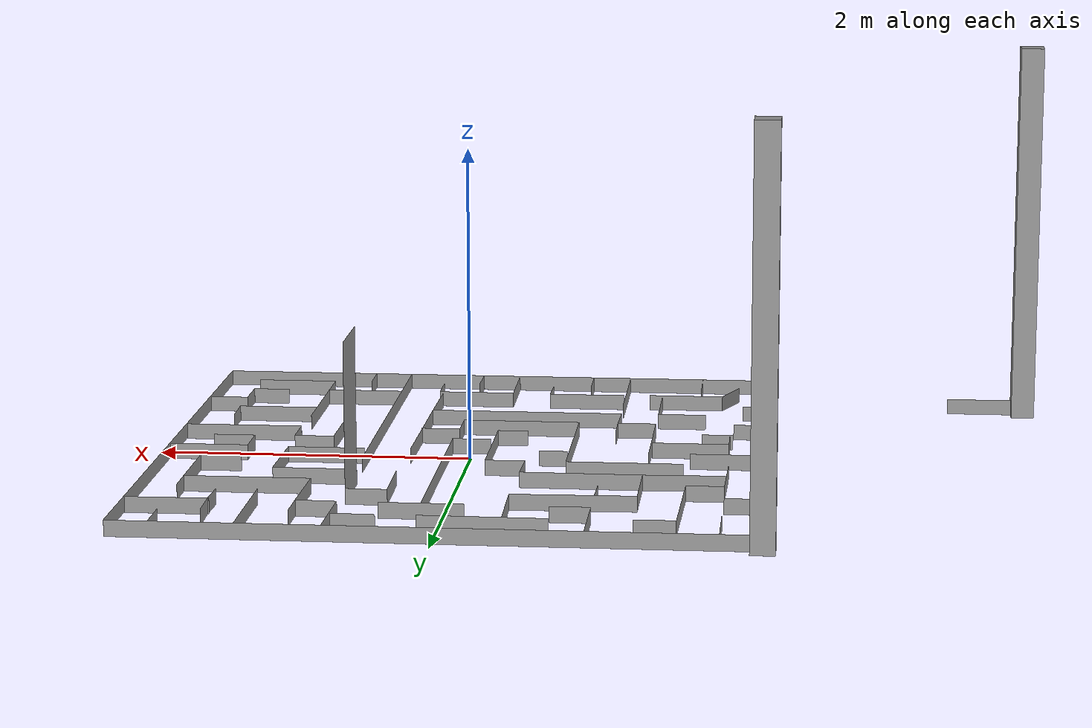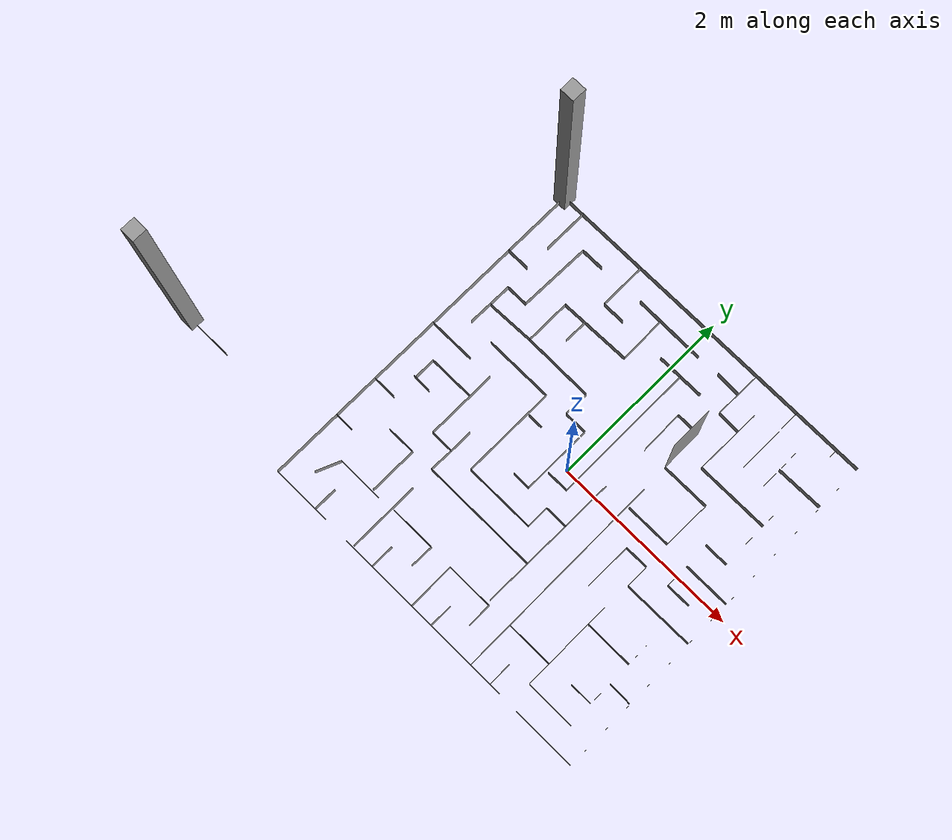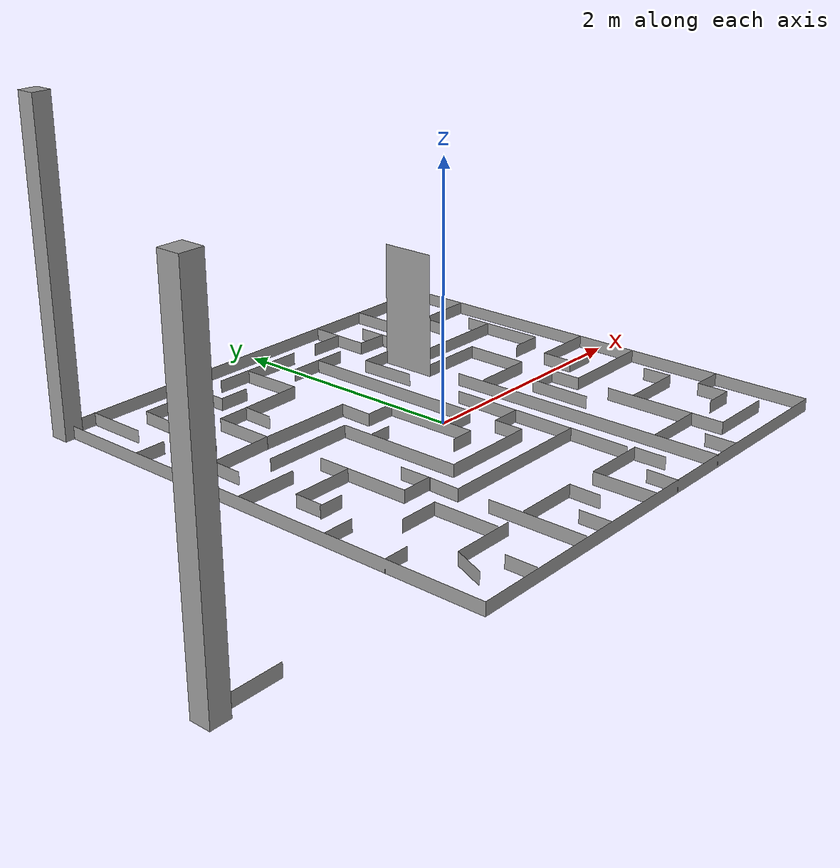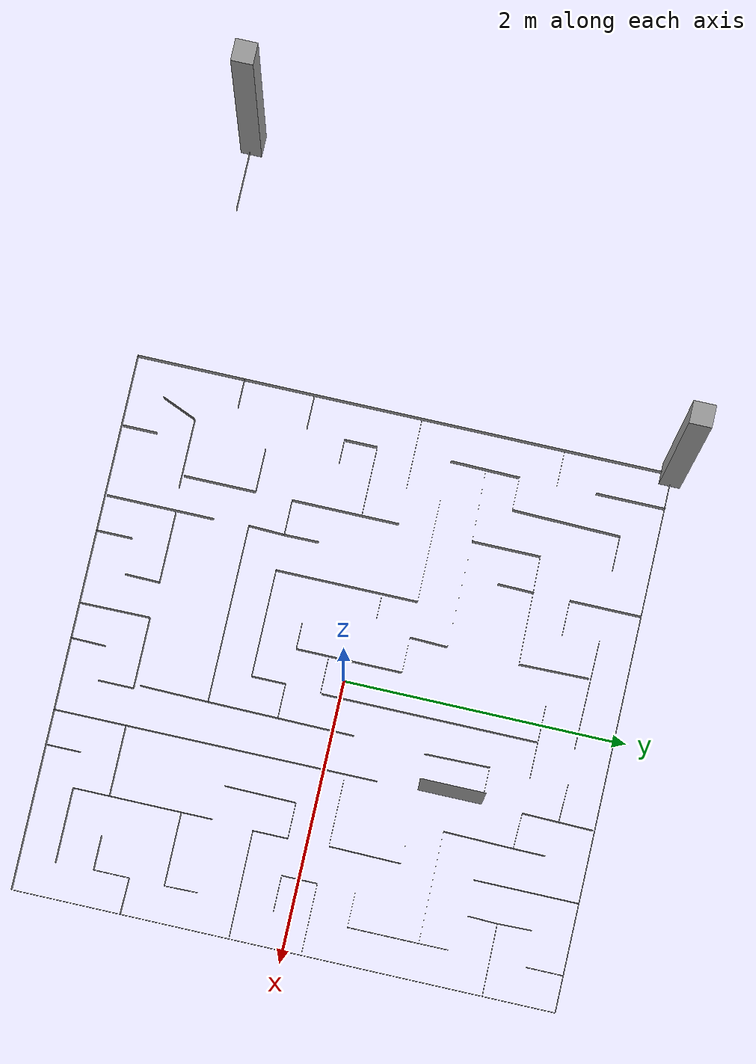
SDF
<?xml version='1.0'?>
<sdf version='1.7'>
  <model name='Untitled'>
    <pose>-0.869381 0.038188 0 0 -0 0</pose>
    <link name='Wall_0'>
      <collision name='Wall_0_Collision'>
        <geometry>
          <box>
            <size>3.825 0 0.1</size>
          </box>
        </geometry>
        <pose>0 0 0.05 0 -0 0</pose>
      </collision>
      <visual name='Wall_0_Visual'>
        <pose>0 0 0.05 0 -0 0</pose>
        <geometry>
          <box>
            <size>3.825 0 0.1</size>
          </box>
        </geometry>
        <material>
          <script>
            <uri>file://media/materials/scripts/gazebo.material</uri>
            <name>Gazebo/Grey</name>
          </script>
          <ambient>1 1 1 1</ambient>
        </material>
        <meta>
          <layer>0</layer>
        </meta>
      </visual>
      <pose>0.872261 -1.94891 0 0 -0 0</pose>
    </link>
    <link name='Wall_101'>
      <collision name='Wall_101_Collision'>
        <geometry>
          <box>
            <size>0.501251 0 0.1</size>
          </box>
        </geometry>
        <pose>0 0 0.05 0 -0 0</pose>
      </collision>
      <visual name='Wall_101_Visual'>
        <pose>0 0 0.05 0 -0 0</pose>
        <geometry>
          <box>
            <size>0.501251 0 0.1</size>
          </box>
        </geometry>
        <material>
          <script>
            <uri>file://media/materials/scripts/gazebo.material</uri>
            <name>Gazebo/Grey</name>
          </script>
          <ambient>1 1 1 1</ambient>
        </material>
        <meta>
          <layer>0</layer>
        </meta>
      </visual>
      <pose>1.50388 1.61431 0 0 -0 -1.58876</pose>
    </link>
    <link name='Wall_102'>
      <collision name='Wall_102_Collision'>
        <geometry>
          <box>
            <size>0.251161 0 0.1</size>
          </box>
        </geometry>
        <pose>0 0 0.05 0 -0 0</pose>
      </collision>
      <visual name='Wall_102_Visual'>
        <pose>0 0 0.05 0 -0 0</pose>
        <geometry>
          <box>
            <size>0.251161 0 0.1</size>
          </box>
        </geometry>
        <material>
          <script>
            <uri>file://media/materials/scripts/gazebo.material</uri>
            <name>Gazebo/Grey</name>
          </script>
          <ambient>1 1 1 1</ambient>
        </material>
        <meta>
          <layer>0</layer>
        </meta>
      </visual>
      <pose>1.62488 1.35931 0 0 -0 -0.035841</pose>
    </link>
    <link name='Wall_103'>
      <collision name='Wall_103_Collision'>
        <geometry>
          <box>
            <size>0.492751 0 0.1</size>
          </box>
        </geometry>
        <pose>0 0 0.05 0 -0 0</pose>
      </collision>
      <visual name='Wall_103_Visual'>
        <pose>0 0 0.05 0 -0 0</pose>
        <geometry>
          <box>
            <size>0.492751 0 0.1</size>
          </box>
        </geometry>
        <material>
          <script>
            <uri>file://media/materials/scripts/gazebo.material</uri>
            <name>Gazebo/Grey</name>
          </script>
          <ambient>1 1 1 1</ambient>
        </material>
        <meta>
          <layer>0</layer>
        </meta>
      </visual>
      <pose>1.74588 1.10831 0 0 -0 -1.58905</pose>
    </link>
    <link name='Wall_104'>
      <collision name='Wall_104_Collision'>
        <geometry>
          <box>
            <size>0.786968 0 0.1</size>
          </box>
        </geometry>
        <pose>0 0 0.05 0 -0 0</pose>
      </collision>
      <visual name='Wall_104_Visual'>
        <pose>0 0 0.05 0 -0 0</pose>
        <geometry>
          <box>
            <size>0.786968 0 0.1</size>
          </box>
        </geometry>
        <material>
          <script>
            <uri>file://media/materials/scripts/gazebo.material</uri>
            <name>Gazebo/Grey</name>
          </script>
          <ambient>1 1 1 1</ambient>
        </material>
        <meta>
          <layer>0</layer>
        </meta>
      </visual>
      <pose>2.13488 0.861812 0 0 -0 0</pose>
    </link>
    <link name='Wall_105'>
      <collision name='Wall_105_Collision'>
        <geometry>
          <box>
            <size>0.501171 0 0.1</size>
          </box>
        </geometry>
        <pose>0 0 0.05 0 -0 0</pose>
      </collision>
      <visual name='Wall_105_Visual'>
        <pose>0 0 0.05 0 -0 0</pose>
        <geometry>
          <box>
            <size>0.501171 0 0.1</size>
          </box>
        </geometry>
        <material>
          <script>
            <uri>file://media/materials/scripts/gazebo.material</uri>
            <name>Gazebo/Grey</name>
          </script>
          <ambient>1 1 1 1</ambient>
        </material>
        <meta>
          <layer>0</layer>
        </meta>
      </visual>
      <pose>2.52838 0.611312 0 0 -0 -1.5708</pose>
    </link>
    <link name='Wall_106'>
      <collision name='Wall_106_Collision'>
        <geometry>
          <box>
            <size>0.259429 0 0.1</size>
          </box>
        </geometry>
        <pose>0 0 0.05 0 -0 0</pose>
      </collision>
      <visual name='Wall_106_Visual'>
        <pose>0 0 0.05 0 -0 0</pose>
        <geometry>
          <box>
            <size>0.259429 0 0.1</size>
          </box>
        </geometry>
        <material>
          <script>
            <uri>file://media/materials/scripts/gazebo.material</uri>
            <name>Gazebo/Grey</name>
          </script>
          <ambient>1 1 1 1</ambient>
        </material>
        <meta>
          <layer>0</layer>
        </meta>
      </visual>
      <pose>2.39888 0.360812 0 0 -0 3.14159</pose>
    </link>
    <link name='Wall_108'>
      <collision name='Wall_108_Collision'>
        <geometry>
          <box>
            <size>0.208821 0 0.1</size>
          </box>
        </geometry>
        <pose>0 0 0.05 0 -0 0</pose>
      </collision>
      <visual name='Wall_108_Visual'>
        <pose>0 0 0.05 0 -0 0</pose>
        <geometry>
          <box>
            <size>0.208821 0 0.1</size>
          </box>
        </geometry>
        <material>
          <script>
            <uri>file://media/materials/scripts/gazebo.material</uri>
            <name>Gazebo/Grey</name>
          </script>
          <ambient>1 1 1 1</ambient>
        </material>
        <meta>
          <layer>0</layer>
        </meta>
      </visual>
      <pose>2.52788 0.966312 0 0 -0 1.57558</pose>
    </link>
    <link name='Wall_110'>
      <collision name='Wall_110_Collision'>
        <geometry>
          <box>
            <size>0.227103 0 0.1</size>
          </box>
        </geometry>
        <pose>0 0 0.05 0 -0 0</pose>
      </collision>
      <visual name='Wall_110_Visual'>
        <pose>0 0 0.05 0 -0 0</pose>
        <geometry>
          <box>
            <size>0.227103 0 0.1</size>
          </box>
        </geometry>
        <material>
          <script>
            <uri>file://media/materials/scripts/gazebo.material</uri>
            <name>Gazebo/Grey</name>
          </script>
          <ambient>1 1 1 1</ambient>
        </material>
        <meta>
          <layer>0</layer>
        </meta>
      </visual>
      <pose>1.75138 1.46831 0 0 -0 1.56199</pose>
    </link>
    <link name='Wall_113'>
      <collision name='Wall_113_Collision'>
        <geometry>
          <box>
            <size>0.268095 0 0.1</size>
          </box>
        </geometry>
        <pose>0 0 0.05 0 -0 0</pose>
      </collision>
      <visual name='Wall_113_Visual'>
        <pose>0 0 0.05 0 -0 0</pose>
        <geometry>
          <box>
            <size>0.268095 0 0.1</size>
          </box>
        </geometry>
        <material>
          <script>
            <uri>file://media/materials/scripts/gazebo.material</uri>
            <name>Gazebo/Grey</name>
          </script>
          <ambient>1 1 1 1</ambient>
        </material>
        <meta>
          <layer>0</layer>
        </meta>
      </visual>
      <pose>1.36538 1.62631 0 0 -0 3.10802</pose>
    </link>
    <link name='Wall_115'>
      <collision name='Wall_115_Collision'>
        <geometry>
          <box>
            <size>0.778287 0 0.1</size>
          </box>
        </geometry>
        <pose>0 0 0.05 0 -0 0</pose>
      </collision>
      <visual name='Wall_115_Visual'>
        <pose>0 0 0.05 0 -0 0</pose>
        <geometry>
          <box>
            <size>0.778287 0 0.1</size>
          </box>
        </geometry>
        <material>
          <script>
            <uri>file://media/materials/scripts/gazebo.material</uri>
            <name>Gazebo/Grey</name>
          </script>
          <ambient>1 1 1 1</ambient>
        </material>
        <meta>
          <layer>0</layer>
        </meta>
      </visual>
      <pose>0.600381 1.62631 0 0 -0 3.13002</pose>
    </link>
    <link name='Wall_117'>
      <collision name='Wall_117_Collision'>
        <geometry>
          <box>
            <size>0.493111 0 0.1</size>
          </box>
        </geometry>
        <pose>0 0 0.05 0 -0 0</pose>
      </collision>
      <visual name='Wall_117_Visual'>
        <pose>0 0 0.05 0 -0 0</pose>
        <geometry>
          <box>
            <size>0.493111 0 0.1</size>
          </box>
        </geometry>
        <material>
          <script>
            <uri>file://media/materials/scripts/gazebo.material</uri>
            <name>Gazebo/Grey</name>
          </script>
          <ambient>1 1 1 1</ambient>
        </material>
        <meta>
          <layer>0</layer>
        </meta>
      </visual>
      <pose>0.491881 1.36731 0 0 -0 -1.55254</pose>
    </link>
    <link name='Wall_118'>
      <collision name='Wall_118_Collision'>
        <geometry>
          <box>
            <size>0.769188 0 0.1</size>
          </box>
        </geometry>
        <pose>0 0 0.05 0 -0 0</pose>
      </collision>
      <visual name='Wall_118_Visual'>
        <pose>0 0 0.05 0 -0 0</pose>
        <geometry>
          <box>
            <size>0.769188 0 0.1</size>
          </box>
        </geometry>
        <material>
          <script>
            <uri>file://media/materials/scripts/gazebo.material</uri>
            <name>Gazebo/Grey</name>
          </script>
          <ambient>1 1 1 1</ambient>
        </material>
        <meta>
          <layer>0</layer>
        </meta>
      </visual>
      <pose>0.111881 1.11231 0 0 -0 -3.11949</pose>
    </link>
    <link name='Wall_119'>
      <collision name='Wall_119_Collision'>
        <geometry>
          <box>
            <size>0.484527 0 0.1</size>
          </box>
        </geometry>
        <pose>0 0 0.05 0 -0 0</pose>
      </collision>
      <visual name='Wall_119_Visual'>
        <pose>0 0 0.05 0 -0 0</pose>
        <geometry>
          <box>
            <size>0.484527 0 0.1</size>
          </box>
        </geometry>
        <material>
          <script>
            <uri>file://media/materials/scripts/gazebo.material</uri>
            <name>Gazebo/Grey</name>
          </script>
          <ambient>1 1 1 1</ambient>
        </material>
        <meta>
          <layer>0</layer>
        </meta>
      </visual>
      <pose>-0.272619 0.861312 0 0 -0 -1.5708</pose>
    </link>
    <link name='Wall_120'>
      <collision name='Wall_120_Collision'>
        <geometry>
          <box>
            <size>0.7605 0 0.1</size>
          </box>
        </geometry>
        <pose>0 0 0.05 0 -0 0</pose>
      </collision>
      <visual name='Wall_120_Visual'>
        <pose>0 0 0.05 0 -0 0</pose>
        <geometry>
          <box>
            <size>0.7605 0 0.1</size>
          </box>
        </geometry>
        <material>
          <script>
            <uri>file://media/materials/scripts/gazebo.material</uri>
            <name>Gazebo/Grey</name>
          </script>
          <ambient>1 1 1 1</ambient>
        </material>
        <meta>
          <layer>0</layer>
        </meta>
      </visual>
      <pose>0.107381 0.614812 0 0 -0 -0.010526</pose>
    </link>
    <link name='Wall_121'>
      <collision name='Wall_121_Collision'>
        <geometry>
          <box>
            <size>0.268341 0 0.1</size>
          </box>
        </geometry>
        <pose>0 0 0.05 0 -0 0</pose>
      </collision>
      <visual name='Wall_121_Visual'>
        <pose>0 0 0.05 0 -0 0</pose>
        <geometry>
          <box>
            <size>0.268341 0 0.1</size>
          </box>
        </geometry>
        <material>
          <script>
            <uri>file://media/materials/scripts/gazebo.material</uri>
            <name>Gazebo/Grey</name>
          </script>
          <ambient>1 1 1 1</ambient>
        </material>
        <meta>
          <layer>0</layer>
        </meta>
      </visual>
      <pose>0.483381 0.476812 0 0 -0 -1.60064</pose>
    </link>
    <link name='Wall_122'>
      <collision name='Wall_122_Collision'>
        <geometry>
          <box>
            <size>0.25056 0 0.1</size>
          </box>
        </geometry>
        <pose>0 0 0.05 0 -0 0</pose>
      </collision>
      <visual name='Wall_122_Visual'>
        <pose>0 0 0.05 0 -0 0</pose>
        <geometry>
          <box>
            <size>0.25056 0 0.1</size>
          </box>
        </geometry>
        <material>
          <script>
            <uri>file://media/materials/scripts/gazebo.material</uri>
            <name>Gazebo/Grey</name>
          </script>
          <ambient>1 1 1 1</ambient>
        </material>
        <meta>
          <layer>0</layer>
        </meta>
      </visual>
      <pose>0.604881 0.342812 0 0 -0 0</pose>
    </link>
    <link name='Wall_123'>
      <collision name='Wall_123_Collision'>
        <geometry>
          <box>
            <size>0.752467 0 0.1</size>
          </box>
        </geometry>
        <pose>0 0 0.05 0 -0 0</pose>
      </collision>
      <visual name='Wall_123_Visual'>
        <pose>0 0 0.05 0 -0 0</pose>
        <geometry>
          <box>
            <size>0.752467 0 0.1</size>
          </box>
        </geometry>
        <material>
          <script>
            <uri>file://media/materials/scripts/gazebo.material</uri>
            <name>Gazebo/Grey</name>
          </script>
          <ambient>1 1 1 1</ambient>
        </material>
        <meta>
          <layer>0</layer>
        </meta>
      </visual>
      <pose>0.730381 -0.033188 0 0 -0 -1.5708</pose>
    </link>
    <link name='Wall_125'>
      <collision name='Wall_125_Collision'>
        <geometry>
          <box>
            <size>0.492984 0 0.1</size>
          </box>
        </geometry>
        <pose>0 0 0.05 0 -0 0</pose>
      </collision>
      <visual name='Wall_125_Visual'>
        <pose>0 0 0.05 0 -0 0</pose>
        <geometry>
          <box>
            <size>0.492984 0 0.1</size>
          </box>
        </geometry>
        <material>
          <script>
            <uri>file://media/materials/scripts/gazebo.material</uri>
            <name>Gazebo/Grey</name>
          </script>
          <ambient>1 1 1 1</ambient>
        </material>
        <meta>
          <layer>0</layer>
        </meta>
      </visual>
      <pose>-0.791619 1.63531 0 0 -0 -1.5708</pose>
    </link>
    <link name='Wall_127'>
      <collision name='Wall_127_Collision'>
        <geometry>
          <box>
            <size>0.250837 0 0.1</size>
          </box>
        </geometry>
        <pose>0 0 0.05 0 -0 0</pose>
      </collision>
      <visual name='Wall_127_Visual'>
        <pose>0 0 0.05 0 -0 0</pose>
        <geometry>
          <box>
            <size>0.250837 0 0.1</size>
          </box>
        </geometry>
        <material>
          <script>
            <uri>file://media/materials/scripts/gazebo.material</uri>
            <name>Gazebo/Grey</name>
          </script>
          <ambient>1 1 1 1</ambient>
        </material>
        <meta>
          <layer>0</layer>
        </meta>
      </visual>
      <pose>-0.407119 1.61381 0 0 -0 3.14159</pose>
    </link>
    <link name='Wall_128'>
      <collision name='Wall_128_Collision'>
        <geometry>
          <box>
            <size>0.769907 0 0.1</size>
          </box>
        </geometry>
        <pose>0 0 0.05 0 -0 0</pose>
      </collision>
      <visual name='Wall_128_Visual'>
        <pose>0 0 0.05 0 -0 0</pose>
        <geometry>
          <box>
            <size>0.769907 0 0.1</size>
          </box>
        </geometry>
        <material>
          <script>
            <uri>file://media/materials/scripts/gazebo.material</uri>
            <name>Gazebo/Grey</name>
          </script>
          <ambient>1 1 1 1</ambient>
        </material>
        <meta>
          <layer>0</layer>
        </meta>
      </visual>
      <pose>-0.541119 1.22881 0 0 -0 -1.59287</pose>
    </link>
    <link name='Wall_129'>
      <collision name='Wall_129_Collision'>
        <geometry>
          <box>
            <size>0.233587 0 0.1</size>
          </box>
        </geometry>
        <pose>0 0 0.05 0 -0 0</pose>
      </collision>
      <visual name='Wall_129_Visual'>
        <pose>0 0 0.05 0 -0 0</pose>
        <geometry>
          <box>
            <size>0.233587 0 0.1</size>
          </box>
        </geometry>
        <material>
          <script>
            <uri>file://media/materials/scripts/gazebo.material</uri>
            <name>Gazebo/Grey</name>
          </script>
          <ambient>1 1 1 1</ambient>
        </material>
        <meta>
          <layer>0</layer>
        </meta>
      </visual>
      <pose>-0.666619 0.843812 0 0 -0 3.14159</pose>
    </link>
    <link name='Wall_130'>
      <collision name='Wall_130_Collision'>
        <geometry>
          <box>
            <size>0.493065 0 0.1</size>
          </box>
        </geometry>
        <pose>0 0 0.05 0 -0 0</pose>
      </collision>
      <visual name='Wall_130_Visual'>
        <pose>0 0 0.05 0 -0 0</pose>
        <geometry>
          <box>
            <size>0.493065 0 0.1</size>
          </box>
        </geometry>
        <material>
          <script>
            <uri>file://media/materials/scripts/gazebo.material</uri>
            <name>Gazebo/Grey</name>
          </script>
          <ambient>1 1 1 1</ambient>
        </material>
        <meta>
          <layer>0</layer>
        </meta>
      </visual>
      <pose>-0.787619 0.597312 0 0 -0 -1.58702</pose>
    </link>
    <link name='Wall_132'>
      <collision name='Wall_132_Collision'>
        <geometry>
          <box>
            <size>0.256182 0 0.1</size>
          </box>
        </geometry>
        <pose>0 0 0.05 0 -0 0</pose>
      </collision>
      <visual name='Wall_132_Visual'>
        <pose>0 0 0.05 0 -0 0</pose>
        <geometry>
          <box>
            <size>0.256182 0 0.1</size>
          </box>
        </geometry>
        <material>
          <script>
            <uri>file://media/materials/scripts/gazebo.material</uri>
            <name>Gazebo/Grey</name>
          </script>
          <ambient>1 1 1 1</ambient>
        </material>
        <meta>
          <layer>0</layer>
        </meta>
      </visual>
      <pose>-0.017119 0.985812 0 0 -0 -1.59032</pose>
    </link>
    <link name='Wall_134'>
      <collision name='Wall_134_Collision'>
        <geometry>
          <box>
            <size>0.51708 0 0.1</size>
          </box>
        </geometry>
        <pose>0 0 0.05 0 -0 0</pose>
      </collision>
      <visual name='Wall_134_Visual'>
        <pose>0 0 0.05 0 -0 0</pose>
        <geometry>
          <box>
            <size>0.51708 0 0.1</size>
          </box>
        </geometry>
        <material>
          <script>
            <uri>file://media/materials/scripts/gazebo.material</uri>
            <name>Gazebo/Grey</name>
          </script>
          <ambient>1 1 1 1</ambient>
        </material>
        <meta>
          <layer>0</layer>
        </meta>
      </visual>
      <pose>0.994881 1.36381 0 0 -0 0</pose>
    </link>
    <link name='Wall_136'>
      <collision name='Wall_136_Collision'>
        <geometry>
          <box>
            <size>1.52347 0 0.1</size>
          </box>
        </geometry>
        <pose>0 0 0.05 0 -0 0</pose>
      </collision>
      <visual name='Wall_136_Visual'>
        <pose>0 0 0.05 0 -0 0</pose>
        <geometry>
          <box>
            <size>1.52347 0 0.1</size>
          </box>
        </geometry>
        <material>
          <script>
            <uri>file://media/materials/scripts/gazebo.material</uri>
            <name>Gazebo/Grey</name>
          </script>
          <ambient>1 1 1 1</ambient>
        </material>
        <meta>
          <layer>0</layer>
        </meta>
      </visual>
      <pose>0.997381 0.596312 0 0 -0 -1.5708</pose>
    </link>
    <link name='Wall_140'>
      <collision name='Wall_140_Collision'>
        <geometry>
          <box>
            <size>0.250222 0 0.1</size>
          </box>
        </geometry>
        <pose>0 0 0.05 0 -0 0</pose>
      </collision>
      <visual name='Wall_140_Visual'>
        <pose>0 0 0.05 0 -0 0</pose>
        <geometry>
          <box>
            <size>0.250222 0 0.1</size>
          </box>
        </geometry>
        <material>
          <script>
            <uri>file://media/materials/scripts/gazebo.material</uri>
            <name>Gazebo/Grey</name>
          </script>
          <ambient>1 1 1 1</ambient>
        </material>
        <meta>
          <layer>0</layer>
        </meta>
      </visual>
      <pose>0.878381 -0.177188 0 0 -0 3.14159</pose>
    </link>
    <link name='Wall_142'>
      <collision name='Wall_142_Collision'>
        <geometry>
          <box>
            <size>0.510251 0 0.1</size>
          </box>
        </geometry>
        <pose>0 0 0.05 0 -0 0</pose>
      </collision>
      <visual name='Wall_142_Visual'>
        <pose>0 0 0.05 0 -0 0</pose>
        <geometry>
          <box>
            <size>0.510251 0 0.1</size>
          </box>
        </geometry>
        <material>
          <script>
            <uri>file://media/materials/scripts/gazebo.material</uri>
            <name>Gazebo/Grey</name>
          </script>
          <ambient>1 1 1 1</ambient>
        </material>
        <meta>
          <layer>0</layer>
        </meta>
      </visual>
      <pose>-0.527619 0.610812 0 0 -0 0.031362</pose>
    </link>
    <link name='Wall_144'>
      <collision name='Wall_144_Collision'>
        <geometry>
          <box>
            <size>0.759621 0 0.1</size>
          </box>
        </geometry>
        <pose>0 0 0.05 0 -0 0</pose>
      </collision>
      <visual name='Wall_144_Visual'>
        <pose>0 0 0.05 0 -0 0</pose>
        <geometry>
          <box>
            <size>0.759621 0 0.1</size>
          </box>
        </geometry>
        <material>
          <script>
            <uri>file://media/materials/scripts/gazebo.material</uri>
            <name>Gazebo/Grey</name>
          </script>
          <ambient>1 1 1 1</ambient>
        </material>
        <meta>
          <layer>0</layer>
        </meta>
      </visual>
      <pose>-0.279619 -0.288188 0 0 -0 -1.5708</pose>
    </link>
    <link name='Wall_147'>
      <collision name='Wall_147_Collision'>
        <geometry>
          <box>
            <size>0.48877 0 0.1</size>
          </box>
        </geometry>
        <pose>0 0 0.05 0 -0 0</pose>
      </collision>
      <visual name='Wall_147_Visual'>
        <pose>0 0 0.05 0 -0 0</pose>
        <geometry>
          <box>
            <size>0.48877 0 0.1</size>
          </box>
        </geometry>
        <material>
          <script>
            <uri>file://media/materials/scripts/gazebo.material</uri>
            <name>Gazebo/Grey</name>
          </script>
          <ambient>1 1 1 1</ambient>
        </material>
        <meta>
          <layer>0</layer>
        </meta>
      </visual>
      <pose>-0.531119 -0.171188 0 0 -0 3.14159</pose>
    </link>
    <link name='Wall_148'>
      <collision name='Wall_148_Collision'>
        <geometry>
          <box>
            <size>0.225946 0 0.1</size>
          </box>
        </geometry>
        <pose>0 0 0.05 0 -0 0</pose>
      </collision>
      <visual name='Wall_148_Visual'>
        <pose>0 0 0.05 0 -0 0</pose>
        <geometry>
          <box>
            <size>0.225946 0 0.1</size>
          </box>
        </geometry>
        <material>
          <script>
            <uri>file://media/materials/scripts/gazebo.material</uri>
            <name>Gazebo/Grey</name>
          </script>
          <ambient>1 1 1 1</ambient>
        </material>
        <meta>
          <layer>0</layer>
        </meta>
      </visual>
      <pose>-0.775619 -0.284188 0 0 -0 -1.5708</pose>
    </link>
    <link name='Wall_150'>
      <collision name='Wall_150_Collision'>
        <geometry>
          <box>
            <size>0.248586 0 0.1</size>
          </box>
        </geometry>
        <pose>0 0 0.05 0 -0 0</pose>
      </collision>
      <visual name='Wall_150_Visual'>
        <pose>0 0 0.05 0 -0 0</pose>
        <geometry>
          <box>
            <size>0.248586 0 0.1</size>
          </box>
        </geometry>
        <material>
          <script>
            <uri>file://media/materials/scripts/gazebo.material</uri>
            <name>Gazebo/Grey</name>
          </script>
          <ambient>1 1 1 1</ambient>
        </material>
        <meta>
          <layer>0</layer>
        </meta>
      </visual>
      <pose>-0.155119 -0.668188 0 0 -0 0</pose>
    </link>
    <link name='Wall_153'>
      <collision name='Wall_153_Collision'>
        <geometry>
          <box>
            <size>0.248129 0 0.1</size>
          </box>
        </geometry>
        <pose>0 0 0.05 0 -0 0</pose>
      </collision>
      <visual name='Wall_153_Visual'>
        <pose>0 0 0.05 0 -0 0</pose>
        <geometry>
          <box>
            <size>0.248129 0 0.1</size>
          </box>
        </geometry>
        <material>
          <script>
            <uri>file://media/materials/scripts/gazebo.material</uri>
            <name>Gazebo/Grey</name>
          </script>
          <ambient>1 1 1 1</ambient>
        </material>
        <meta>
          <layer>0</layer>
        </meta>
      </visual>
      <pose>-0.034619 -0.799188 0 0 -0 -1.60304</pose>
    </link>
    <link name='Wall_154'>
      <collision name='Wall_154_Collision'>
        <geometry>
          <box>
            <size>1.263 0 0.1</size>
          </box>
        </geometry>
        <pose>0 0 0.05 0 -0 0</pose>
      </collision>
      <visual name='Wall_154_Visual'>
        <pose>0 0 0.05 0 -0 0</pose>
        <geometry>
          <box>
            <size>1.263 0 0.1</size>
          </box>
        </geometry>
        <material>
          <script>
            <uri>file://media/materials/scripts/gazebo.material</uri>
            <name>Gazebo/Grey</name>
          </script>
          <ambient>1 1 1 1</ambient>
        </material>
        <meta>
          <layer>0</layer>
        </meta>
      </visual>
      <pose>0.592881 -0.923188 0 0 -0 0</pose>
    </link>
    <link name='Wall_155'>
      <collision name='Wall_155_Collision'>
        <geometry>
          <box>
            <size>0.481513 0 0.1</size>
          </box>
        </geometry>
        <pose>0 0 0.05 0 -0 0</pose>
      </collision>
      <visual name='Wall_155_Visual'>
        <pose>0 0 0.05 0 -0 0</pose>
        <geometry>
          <box>
            <size>0.481513 0 0.1</size>
          </box>
        </geometry>
        <material>
          <script>
            <uri>file://media/materials/scripts/gazebo.material</uri>
            <name>Gazebo/Grey</name>
          </script>
          <ambient>1 1 1 1</ambient>
        </material>
        <meta>
          <layer>0</layer>
        </meta>
      </visual>
      <pose>1.22088 -1.16369 0 0 -0 -1.58535</pose>
    </link>
    <link name='Wall_157'>
      <collision name='Wall_157_Collision'>
        <geometry>
          <box>
            <size>0.737 0 0.1</size>
          </box>
        </geometry>
        <pose>0 0 0.05 0 -0 0</pose>
      </collision>
      <visual name='Wall_157_Visual'>
        <pose>0 0 0.05 0 -0 0</pose>
        <geometry>
          <box>
            <size>0.737 0 0.1</size>
          </box>
        </geometry>
        <material>
          <script>
            <uri>file://media/materials/scripts/gazebo.material</uri>
            <name>Gazebo/Grey</name>
          </script>
          <ambient>1 1 1 1</ambient>
        </material>
        <meta>
          <layer>0</layer>
        </meta>
      </visual>
      <pose>-0.144119 0.339812 0 0 -0 0</pose>
    </link>
    <link name='Wall_158'>
      <collision name='Wall_158_Collision'>
        <geometry>
          <box>
            <size>1.00762 0 0.1</size>
          </box>
        </geometry>
        <pose>0 0 0.05 0 -0 0</pose>
      </collision>
      <visual name='Wall_158_Visual'>
        <pose>0 0 0.05 0 -0 0</pose>
        <geometry>
          <box>
            <size>1.00762 0 0.1</size>
          </box>
        </geometry>
        <material>
          <script>
            <uri>file://media/materials/scripts/gazebo.material</uri>
            <name>Gazebo/Grey</name>
          </script>
          <ambient>1 1 1 1</ambient>
        </material>
        <meta>
          <layer>0</layer>
        </meta>
      </visual>
      <pose>0.224381 -0.164188 0 0 -0 -1.5708</pose>
    </link>
    <link name='Wall_159'>
      <collision name='Wall_159_Collision'>
        <geometry>
          <box>
            <size>0.759616 0 0.1</size>
          </box>
        </geometry>
        <pose>0 0 0.05 0 -0 0</pose>
      </collision>
      <visual name='Wall_159_Visual'>
        <pose>0 0 0.05 0 -0 0</pose>
        <geometry>
          <box>
            <size>0.759616 0 0.1</size>
          </box>
        </geometry>
        <material>
          <script>
            <uri>file://media/materials/scripts/gazebo.material</uri>
            <name>Gazebo/Grey</name>
          </script>
          <ambient>1 1 1 1</ambient>
        </material>
        <meta>
          <layer>0</layer>
        </meta>
      </visual>
      <pose>0.604381 -0.668188 0 0 -0 0</pose>
    </link>
    <link name='Wall_16'>
      <collision name='Wall_16_Collision'>
        <geometry>
          <box>
            <size>0.505 0 0.1</size>
          </box>
        </geometry>
        <pose>0 0 0.05 0 -0 0</pose>
      </collision>
      <visual name='Wall_16_Visual'>
        <pose>0 0 0.05 0 -0 0</pose>
        <geometry>
          <box>
            <size>0.505 0 0.1</size>
          </box>
        </geometry>
        <material>
          <script>
            <uri>file://media/materials/scripts/gazebo.material</uri>
            <name>Gazebo/Grey</name>
          </script>
          <ambient>1 1 1 1</ambient>
        </material>
        <meta>
          <layer>0</layer>
        </meta>
      </visual>
      <pose>-0.015163 1.62216 0 0 -0 -1.5708</pose>
    </link>
    <link name='Wall_160'>
      <collision name='Wall_160_Collision'>
        <geometry>
          <box>
            <size>0.241 0 0.1</size>
          </box>
        </geometry>
        <pose>0 0 0.05 0 -0 0</pose>
      </collision>
      <visual name='Wall_160_Visual'>
        <pose>0 0 0.05 0 -0 0</pose>
        <geometry>
          <box>
            <size>0.241 0 0.1</size>
          </box>
        </geometry>
        <material>
          <script>
            <uri>file://media/materials/scripts/gazebo.material</uri>
            <name>Gazebo/Grey</name>
          </script>
          <ambient>1 1 1 1</ambient>
        </material>
        <meta>
          <layer>0</layer>
        </meta>
      </visual>
      <pose>0.984381 -0.547688 0 0 -0 1.5708</pose>
    </link>
    <link name='Wall_161'>
      <collision name='Wall_161_Collision'>
        <geometry>
          <box>
            <size>0.247734 0 0.1</size>
          </box>
        </geometry>
        <pose>0 0 0.05 0 -0 0</pose>
      </collision>
      <visual name='Wall_161_Visual'>
        <pose>0 0 0.05 0 -0 0</pose>
        <geometry>
          <box>
            <size>0.247734 0 0.1</size>
          </box>
        </geometry>
        <material>
          <script>
            <uri>file://media/materials/scripts/gazebo.material</uri>
            <name>Gazebo/Grey</name>
          </script>
          <ambient>1 1 1 1</ambient>
        </material>
        <meta>
          <layer>0</layer>
        </meta>
      </visual>
      <pose>1.10838 -0.427188 0 0 -0 0</pose>
    </link>
    <link name='Wall_163'>
      <collision name='Wall_163_Collision'>
        <geometry>
          <box>
            <size>1.03736 0 0.1</size>
          </box>
        </geometry>
        <pose>0 0 0.05 0 -0 0</pose>
      </collision>
      <visual name='Wall_163_Visual'>
        <pose>0 0 0.05 0 -0 0</pose>
        <geometry>
          <box>
            <size>1.03736 0 0.1</size>
          </box>
        </geometry>
        <material>
          <script>
            <uri>file://media/materials/scripts/gazebo.material</uri>
            <name>Gazebo/Grey</name>
          </script>
          <ambient>1 1 1 1</ambient>
        </material>
        <meta>
          <layer>0</layer>
        </meta>
      </visual>
      <pose>1.22838 -0.404688 0 0 -0 1.56308</pose>
    </link>
    <link name='Wall_165'>
      <collision name='Wall_165_Collision'>
        <geometry>
          <box>
            <size>0.458792 0 0.1</size>
          </box>
        </geometry>
        <pose>0 0 0.05 0 -0 0</pose>
      </collision>
      <visual name='Wall_165_Visual'>
        <pose>0 0 0.05 0 -0 0</pose>
        <geometry>
          <box>
            <size>0.458792 0 0.1</size>
          </box>
        </geometry>
        <material>
          <script>
            <uri>file://media/materials/scripts/gazebo.material</uri>
            <name>Gazebo/Grey</name>
          </script>
          <ambient>1 1 1 1</ambient>
        </material>
        <meta>
          <layer>0</layer>
        </meta>
      </visual>
      <pose>1.24338 0.847312 0 0 -0 1.58822</pose>
    </link>
    <link name='Wall_166'>
      <collision name='Wall_166_Collision'>
        <geometry>
          <box>
            <size>0.256 0 0.1</size>
          </box>
        </geometry>
        <pose>0 0 0.05 0 -0 0</pose>
      </collision>
      <visual name='Wall_166_Visual'>
        <pose>0 0 0.05 0 -0 0</pose>
        <geometry>
          <box>
            <size>0.256 0 0.1</size>
          </box>
        </geometry>
        <material>
          <script>
            <uri>file://media/materials/scripts/gazebo.material</uri>
            <name>Gazebo/Grey</name>
          </script>
          <ambient>1 1 1 1</ambient>
        </material>
        <meta>
          <layer>0</layer>
        </meta>
      </visual>
      <pose>1.36738 1.07681 0 0 -0 0</pose>
    </link>
    <link name='Wall_167'>
      <collision name='Wall_167_Collision'>
        <geometry>
          <box>
            <size>0.451398 0 1</size>
          </box>
        </geometry>
        <pose>0 0 0.5 0 -0 0</pose>
      </collision>
      <visual name='Wall_167_Visual'>
        <pose>0 0 0.5 0 -0 0</pose>
        <geometry>
          <box>
            <size>0.451398 0 1</size>
          </box>
        </geometry>
        <material>
          <script>
            <uri>file://media/materials/scripts/gazebo.material</uri>
            <name>Gazebo/Grey</name>
          </script>
          <ambient>1 1 1 1</ambient>
        </material>
        <meta>
          <layer>0</layer>
        </meta>
      </visual>
      <pose>1.49538 0.851312 0 0 -0 -1.5708</pose>
    </link>
    <link name='Wall_168'>
      <collision name='Wall_168_Collision'>
        <geometry>
          <box>
            <size>0.526202 0 0.1</size>
          </box>
        </geometry>
        <pose>0 0 0.05 0 -0 0</pose>
      </collision>
      <visual name='Wall_168_Visual'>
        <pose>0 0 0.05 0 -0 0</pose>
        <geometry>
          <box>
            <size>0.526202 0 0.1</size>
          </box>
        </geometry>
        <material>
          <script>
            <uri>file://media/materials/scripts/gazebo.material</uri>
            <name>Gazebo/Grey</name>
          </script>
          <ambient>1 1 1 1</ambient>
        </material>
        <meta>
          <layer>0</layer>
        </meta>
      </visual>
      <pose>1.75838 0.625812 0 0 -0 0</pose>
    </link>
    <link name='Wall_169'>
      <collision name='Wall_169_Collision'>
        <geometry>
          <box>
            <size>0.511724 0 0.1</size>
          </box>
        </geometry>
        <pose>0 0 0.05 0 -0 0</pose>
      </collision>
      <visual name='Wall_169_Visual'>
        <pose>0 0 0.05 0 -0 0</pose>
        <geometry>
          <box>
            <size>0.511724 0 0.1</size>
          </box>
        </geometry>
        <material>
          <script>
            <uri>file://media/materials/scripts/gazebo.material</uri>
            <name>Gazebo/Grey</name>
          </script>
          <ambient>1 1 1 1</ambient>
        </material>
        <meta>
          <layer>0</layer>
        </meta>
      </visual>
      <pose>2.01788 0.369812 0 0 -0 -1.58447</pose>
    </link>
    <link name='Wall_170'>
      <collision name='Wall_170_Collision'>
        <geometry>
          <box>
            <size>0.489035 0 0.1</size>
          </box>
        </geometry>
        <pose>0 0 0.05 0 -0 0</pose>
      </collision>
      <visual name='Wall_170_Visual'>
        <pose>0 0 0.05 0 -0 0</pose>
        <geometry>
          <box>
            <size>0.489035 0 0.1</size>
          </box>
        </geometry>
        <material>
          <script>
            <uri>file://media/materials/scripts/gazebo.material</uri>
            <name>Gazebo/Grey</name>
          </script>
          <ambient>1 1 1 1</ambient>
        </material>
        <meta>
          <layer>0</layer>
        </meta>
      </visual>
      <pose>1.76988 0.113812 0 0 -0 3.14159</pose>
    </link>
    <link name='Wall_172'>
      <collision name='Wall_172_Collision'>
        <geometry>
          <box>
            <size>0.252962 0 0.1</size>
          </box>
        </geometry>
        <pose>0 0 0.05 0 -0 0</pose>
      </collision>
      <visual name='Wall_172_Visual'>
        <pose>0 0 0.05 0 -0 0</pose>
        <geometry>
          <box>
            <size>0.252962 0 0.1</size>
          </box>
        </geometry>
        <material>
          <script>
            <uri>file://media/materials/scripts/gazebo.material</uri>
            <name>Gazebo/Grey</name>
          </script>
          <ambient>1 1 1 1</ambient>
        </material>
        <meta>
          <layer>0</layer>
        </meta>
      </visual>
      <pose>-0.031619 -0.548688 0 0 -0 1.5787</pose>
    </link>
    <link name='Wall_174'>
      <collision name='Wall_174_Collision'>
        <geometry>
          <box>
            <size>0.176052 0 0.1</size>
          </box>
        </geometry>
        <pose>0 0 0.05 0 -0 0</pose>
      </collision>
      <visual name='Wall_174_Visual'>
        <pose>0 0 0.05 0 -0 0</pose>
        <geometry>
          <box>
            <size>0.176052 0 0.1</size>
          </box>
        </geometry>
        <material>
          <script>
            <uri>file://media/materials/scripts/gazebo.material</uri>
            <name>Gazebo/Grey</name>
          </script>
          <ambient>1 1 1 1</ambient>
        </material>
        <meta>
          <layer>0</layer>
        </meta>
      </visual>
      <pose>0.324381 0.087812 0 0 -0 0</pose>
    </link>
    <link name='Wall_176'>
      <collision name='Wall_176_Collision'>
        <geometry>
          <box>
            <size>0.193726 0 0.1</size>
          </box>
        </geometry>
        <pose>0 0 0.05 0 -0 0</pose>
      </collision>
      <visual name='Wall_176_Visual'>
        <pose>0 0 0.05 0 -0 0</pose>
        <geometry>
          <box>
            <size>0.193726 0 0.1</size>
          </box>
        </geometry>
        <material>
          <script>
            <uri>file://media/materials/scripts/gazebo.material</uri>
            <name>Gazebo/Grey</name>
          </script>
          <ambient>1 1 1 1</ambient>
        </material>
        <meta>
          <layer>0</layer>
        </meta>
      </visual>
      <pose>0.633381 -0.409188 0 0 -0 3.14159</pose>
    </link>
    <link name='Wall_180'>
      <collision name='Wall_180_Collision'>
        <geometry>
          <box>
            <size>0.512 0 0.1</size>
          </box>
        </geometry>
        <pose>0 0 0.05 0 -0 0</pose>
      </collision>
      <visual name='Wall_180_Visual'>
        <pose>0 0 0.05 0 -0 0</pose>
        <geometry>
          <box>
            <size>0.512 0 0.1</size>
          </box>
        </geometry>
        <material>
          <script>
            <uri>file://media/materials/scripts/gazebo.material</uri>
            <name>Gazebo/Grey</name>
          </script>
          <ambient>1 1 1 1</ambient>
        </material>
        <meta>
          <layer>0</layer>
        </meta>
      </visual>
      <pose>-0.281619 -1.18519 0 0 -0 1.5708</pose>
    </link>
    <link name='Wall_181'>
      <collision name='Wall_181_Collision'>
        <geometry>
          <box>
            <size>0.312709 0 0.1</size>
          </box>
        </geometry>
        <pose>0 0 0.05 0 -0 0</pose>
      </collision>
      <visual name='Wall_181_Visual'>
        <pose>0 0 0.05 0 -0 0</pose>
        <geometry>
          <box>
            <size>0.312709 0 0.1</size>
          </box>
        </geometry>
        <material>
          <script>
            <uri>file://media/materials/scripts/gazebo.material</uri>
            <name>Gazebo/Grey</name>
          </script>
          <ambient>1 1 1 1</ambient>
        </material>
        <meta>
          <layer>0</layer>
        </meta>
      </visual>
      <pose>-0.438119 -0.929188 0 0 -0 3.14159</pose>
    </link>
    <link name='Wall_186'>
      <collision name='Wall_186_Collision'>
        <geometry>
          <box>
            <size>0.199 0 0.1</size>
          </box>
        </geometry>
        <pose>0 0 0.05 0 -0 0</pose>
      </collision>
      <visual name='Wall_186_Visual'>
        <pose>0 0 0.05 0 -0 0</pose>
        <geometry>
          <box>
            <size>0.199 0 0.1</size>
          </box>
        </geometry>
        <material>
          <script>
            <uri>file://media/materials/scripts/gazebo.material</uri>
            <name>Gazebo/Grey</name>
          </script>
          <ambient>1 1 1 1</ambient>
        </material>
        <meta>
          <layer>0</layer>
        </meta>
      </visual>
      <pose>-0.694119 -0.406188 0 0 -0 0</pose>
    </link>
    <link name='Wall_2'>
      <collision name='Wall_2_Collision'>
        <geometry>
          <box>
            <size>3.825 0 0.1</size>
          </box>
        </geometry>
        <pose>0 0 0.05 0 -0 0</pose>
      </collision>
      <visual name='Wall_2_Visual'>
        <pose>0 0 0.05 0 -0 0</pose>
        <geometry>
          <box>
            <size>3.825 0 0.1</size>
          </box>
        </geometry>
        <material>
          <script>
            <uri>file://media/materials/scripts/gazebo.material</uri>
            <name>Gazebo/Grey</name>
          </script>
          <ambient>1 1 1 1</ambient>
        </material>
        <meta>
          <layer>0</layer>
        </meta>
      </visual>
      <pose>2.78476 -0.036406 0 0 -0 1.5708</pose>
    </link>
    <link name='Wall_20'>
      <collision name='Wall_20_Collision'>
        <geometry>
          <box>
            <size>0.25 0 0.1</size>
          </box>
        </geometry>
        <pose>0 0 0.05 0 -0 0</pose>
      </collision>
      <visual name='Wall_20_Visual'>
        <pose>0 0 0.05 0 -0 0</pose>
        <geometry>
          <box>
            <size>0.25 0 0.1</size>
          </box>
        </geometry>
        <material>
          <script>
            <uri>file://media/materials/scripts/gazebo.material</uri>
            <name>Gazebo/Grey</name>
          </script>
          <ambient>1 1 1 1</ambient>
        </material>
        <meta>
          <layer>0</layer>
        </meta>
      </visual>
      <pose>0.109837 1.36966 0 0 -0 0</pose>
    </link>
    <link name='Wall_24'>
      <collision name='Wall_24_Collision'>
        <geometry>
          <box>
            <size>0.15 0.15 2.5</size>
          </box>
        </geometry>
        <pose>0 0 1.25 0 -0 0</pose>
      </collision>
      <visual name='Wall_24_Visual'>
        <pose>0 0 1.25 0 -0 0</pose>
        <geometry>
          <box>
            <size>0.15 0.15 2.5</size>
          </box>
        </geometry>
        <material>
          <script>
            <uri>file://media/materials/scripts/gazebo.material</uri>
            <name>Gazebo/Grey</name>
          </script>
          <ambient>1 1 1 1</ambient>
        </material>
        <meta>
          <layer>0</layer>
        </meta>
      </visual>
      <pose>-1.04024 1.87609 0 0 -0 0</pose>
    </link>
    <link name='Wall_27'>
      <collision name='Wall_27_Collision'>
        <geometry>
          <box>
            <size>0.25 0 0.1</size>
          </box>
        </geometry>
        <pose>0 0 0.05 0 -0 0</pose>
      </collision>
      <visual name='Wall_27_Visual'>
        <pose>0 0 0.05 0 -0 0</pose>
        <geometry>
          <box>
            <size>0.25 0 0.1</size>
          </box>
        </geometry>
        <material>
          <script>
            <uri>file://media/materials/scripts/gazebo.material</uri>
            <name>Gazebo/Grey</name>
          </script>
          <ambient>1 1 1 1</ambient>
        </material>
        <meta>
          <layer>0</layer>
        </meta>
      </visual>
      <pose>-0.915574 1.11098 0 0 -0 0</pose>
    </link>
    <link name='Wall_29'>
      <collision name='Wall_29_Collision'>
        <geometry>
          <box>
            <size>0.495 0 0.1</size>
          </box>
        </geometry>
        <pose>0 0 0.05 0 -0 0</pose>
      </collision>
      <visual name='Wall_29_Visual'>
        <pose>0 0 0.05 0 -0 0</pose>
        <geometry>
          <box>
            <size>0.495 0 0.1</size>
          </box>
        </geometry>
        <material>
          <script>
            <uri>file://media/materials/scripts/gazebo.material</uri>
            <name>Gazebo/Grey</name>
          </script>
          <ambient>1 1 1 1</ambient>
        </material>
        <meta>
          <layer>0</layer>
        </meta>
      </visual>
      <pose>-0.789119 0.090812 0 0 -0 0</pose>
    </link>
    <link name='Wall_31'>
      <collision name='Wall_31_Collision'>
        <geometry>
          <box>
            <size>0.25 0 0.1</size>
          </box>
        </geometry>
        <pose>0 0 0.05 0 -0 0</pose>
      </collision>
      <visual name='Wall_31_Visual'>
        <pose>0 0 0.05 0 -0 0</pose>
        <geometry>
          <box>
            <size>0.25 0 0.1</size>
          </box>
        </geometry>
        <material>
          <script>
            <uri>file://media/materials/scripts/gazebo.material</uri>
            <name>Gazebo/Grey</name>
          </script>
          <ambient>1 1 1 1</ambient>
        </material>
        <meta>
          <layer>0</layer>
        </meta>
      </visual>
      <pose>-0.914602 -0.68064 0 0 -0 0</pose>
    </link>
    <link name='Wall_33'>
      <collision name='Wall_33_Collision'>
        <geometry>
          <box>
            <size>0.205022 0 0.1</size>
          </box>
        </geometry>
        <pose>0 0 0.05 0 -0 0</pose>
      </collision>
      <visual name='Wall_33_Visual'>
        <pose>0 0 0.05 0 -0 0</pose>
        <geometry>
          <box>
            <size>0.205022 0 0.1</size>
          </box>
        </geometry>
        <material>
          <script>
            <uri>file://media/materials/scripts/gazebo.material</uri>
            <name>Gazebo/Grey</name>
          </script>
          <ambient>1 1 1 1</ambient>
        </material>
        <meta>
          <layer>0</layer>
        </meta>
      </visual>
      <pose>-0.939119 -1.18319 0 0 -0 0</pose>
    </link>
    <link name='Wall_35'>
      <collision name='Wall_35_Collision'>
        <geometry>
          <box>
            <size>0.5 0 0.1</size>
          </box>
        </geometry>
        <pose>0 0 0.05 0 -0 0</pose>
      </collision>
      <visual name='Wall_35_Visual'>
        <pose>0 0 0.05 0 -0 0</pose>
        <geometry>
          <box>
            <size>0.5 0 0.1</size>
          </box>
        </geometry>
        <material>
          <script>
            <uri>file://media/materials/scripts/gazebo.material</uri>
            <name>Gazebo/Grey</name>
          </script>
          <ambient>1 1 1 1</ambient>
        </material>
        <meta>
          <layer>0</layer>
        </meta>
      </visual>
      <pose>-2.45976 -1.51086 0 0 -0 0</pose>
    </link>
    <link name='Wall_39'>
      <collision name='Wall_39_Collision'>
        <geometry>
          <box>
            <size>0.15 0.15 2.5</size>
          </box>
        </geometry>
        <pose>0 0 1.25 0 -0 0</pose>
      </collision>
      <visual name='Wall_39_Visual'>
        <pose>0 0 1.25 0 -0 0</pose>
        <geometry>
          <box>
            <size>0.15 0.15 2.5</size>
          </box>
        </geometry>
        <material>
          <script>
            <uri>file://media/materials/scripts/gazebo.material</uri>
            <name>Gazebo/Grey</name>
          </script>
          <ambient>1 1 1 1</ambient>
        </material>
        <meta>
          <layer>0</layer>
        </meta>
      </visual>
      <pose>-2.70976 -1.50221 0 0 -0 0</pose>
    </link>
    <link name='Wall_4'>
      <collision name='Wall_4_Collision'>
        <geometry>
          <box>
            <size>3.825 0 0.1</size>
          </box>
        </geometry>
        <pose>0 0 0.05 0 -0 0</pose>
      </collision>
      <visual name='Wall_4_Visual'>
        <pose>0 0 0.05 0 -0 0</pose>
        <geometry>
          <box>
            <size>3.825 0 0.1</size>
          </box>
        </geometry>
        <material>
          <script>
            <uri>file://media/materials/scripts/gazebo.material</uri>
            <name>Gazebo/Grey</name>
          </script>
          <ambient>1 1 1 1</ambient>
        </material>
        <meta>
          <layer>0</layer>
        </meta>
      </visual>
      <pose>0.872261 1.87609 0 0 -0 3.14159</pose>
    </link>
    <link name='Wall_41'>
      <collision name='Wall_41_Collision'>
        <geometry>
          <box>
            <size>0.245 0 0.1</size>
          </box>
        </geometry>
        <pose>0 0 0.05 0 -0 0</pose>
      </collision>
      <visual name='Wall_41_Visual'>
        <pose>0 0 0.05 0 -0 0</pose>
        <geometry>
          <box>
            <size>0.245 0 0.1</size>
          </box>
        </geometry>
        <material>
          <script>
            <uri>file://media/materials/scripts/gazebo.material</uri>
            <name>Gazebo/Grey</name>
          </script>
          <ambient>1 1 1 1</ambient>
        </material>
        <meta>
          <layer>0</layer>
        </meta>
      </visual>
      <pose>-0.535619 -1.81569 0 0 -0 1.5708</pose>
    </link>
    <link name='Wall_43'>
      <collision name='Wall_43_Collision'>
        <geometry>
          <box>
            <size>0.765 0 0.1</size>
          </box>
        </geometry>
        <pose>0 0 0.05 0 -0 0</pose>
      </collision>
      <visual name='Wall_43_Visual'>
        <pose>0 0 0.05 0 -0 0</pose>
        <geometry>
          <box>
            <size>0.765 0 0.1</size>
          </box>
        </geometry>
        <material>
          <script>
            <uri>file://media/materials/scripts/gazebo.material</uri>
            <name>Gazebo/Grey</name>
          </script>
          <ambient>1 1 1 1</ambient>
        </material>
        <meta>
          <layer>0</layer>
        </meta>
      </visual>
      <pose>-0.030888 -1.55255 0 0 -0 1.5708</pose>
    </link>
    <link name='Wall_45'>
      <collision name='Wall_45_Collision'>
        <geometry>
          <box>
            <size>0.271155 0 0.1</size>
          </box>
        </geometry>
        <pose>0 0 0.05 0 -0 0</pose>
      </collision>
      <visual name='Wall_45_Visual'>
        <pose>0 0 0.05 0 -0 0</pose>
        <geometry>
          <box>
            <size>0.271155 0 0.1</size>
          </box>
        </geometry>
        <material>
          <script>
            <uri>file://media/materials/scripts/gazebo.material</uri>
            <name>Gazebo/Grey</name>
          </script>
          <ambient>1 1 1 1</ambient>
        </material>
        <meta>
          <layer>0</layer>
        </meta>
      </visual>
      <pose>-0.740211 -1.58264 0 0 -0 1.17317</pose>
    </link>
    <link name='Wall_48'>
      <collision name='Wall_48_Collision'>
        <geometry>
          <box>
            <size>0.495 0 0.1</size>
          </box>
        </geometry>
        <pose>0 0 0.05 0 -0 0</pose>
      </collision>
      <visual name='Wall_48_Visual'>
        <pose>0 0 0.05 0 -0 0</pose>
        <geometry>
          <box>
            <size>0.495 0 0.1</size>
          </box>
        </geometry>
        <material>
          <script>
            <uri>file://media/materials/scripts/gazebo.material</uri>
            <name>Gazebo/Grey</name>
          </script>
          <ambient>1 1 1 1</ambient>
        </material>
        <meta>
          <layer>0</layer>
        </meta>
      </visual>
      <pose>-0.440211 -1.45764 0 0 -0 3.14159</pose>
    </link>
    <link name='Wall_50'>
      <collision name='Wall_50_Collision'>
        <geometry>
          <box>
            <size>0.25 0 0.1</size>
          </box>
        </geometry>
        <pose>0 0 0.05 0 -0 0</pose>
      </collision>
      <visual name='Wall_50_Visual'>
        <pose>0 0 0.05 0 -0 0</pose>
        <geometry>
          <box>
            <size>0.25 0 0.1</size>
          </box>
        </geometry>
        <material>
          <script>
            <uri>file://media/materials/scripts/gazebo.material</uri>
            <name>Gazebo/Grey</name>
          </script>
          <ambient>1 1 1 1</ambient>
        </material>
        <meta>
          <layer>0</layer>
        </meta>
      </visual>
      <pose>0.2261 -1.82168 0 0 -0 1.5708</pose>
    </link>
    <link name='Wall_52'>
      <collision name='Wall_52_Collision'>
        <geometry>
          <box>
            <size>0.499025 0 0.1</size>
          </box>
        </geometry>
        <pose>0 0 0.05 0 -0 0</pose>
      </collision>
      <visual name='Wall_52_Visual'>
        <pose>0 0 0.05 0 -0 0</pose>
        <geometry>
          <box>
            <size>0.499025 0 0.1</size>
          </box>
        </geometry>
        <material>
          <script>
            <uri>file://media/materials/scripts/gazebo.material</uri>
            <name>Gazebo/Grey</name>
          </script>
          <ambient>1 1 1 1</ambient>
        </material>
        <meta>
          <layer>0</layer>
        </meta>
      </visual>
      <pose>0.742881 -1.69669 0 0 -0 1.58082</pose>
    </link>
    <link name='Wall_53'>
      <collision name='Wall_53_Collision'>
        <geometry>
          <box>
            <size>0.504706 0 0.1</size>
          </box>
        </geometry>
        <pose>0 0 0.05 0 -0 0</pose>
      </collision>
      <visual name='Wall_53_Visual'>
        <pose>0 0 0.05 0 -0 0</pose>
        <geometry>
          <box>
            <size>0.504706 0 0.1</size>
          </box>
        </geometry>
        <material>
          <script>
            <uri>file://media/materials/scripts/gazebo.material</uri>
            <name>Gazebo/Grey</name>
          </script>
          <ambient>1 1 1 1</ambient>
        </material>
        <meta>
          <layer>0</layer>
        </meta>
      </visual>
      <pose>0.992881 -1.44719 0 0 -0 0</pose>
    </link>
    <link name='Wall_54'>
      <collision name='Wall_54_Collision'>
        <geometry>
          <box>
            <size>0.251915 0 0.1</size>
          </box>
        </geometry>
        <pose>0 0 0.05 0 -0 0</pose>
      </collision>
      <visual name='Wall_54_Visual'>
        <pose>0 0 0.05 0 -0 0</pose>
        <geometry>
          <box>
            <size>0.251915 0 0.1</size>
          </box>
        </geometry>
        <material>
          <script>
            <uri>file://media/materials/scripts/gazebo.material</uri>
            <name>Gazebo/Grey</name>
          </script>
          <ambient>1 1 1 1</ambient>
        </material>
        <meta>
          <layer>0</layer>
        </meta>
      </visual>
      <pose>1.24538 -1.57319 0 0 -0 -1.5708</pose>
    </link>
    <link name='Wall_56'>
      <collision name='Wall_56_Collision'>
        <geometry>
          <box>
            <size>0.247843 0 0.1</size>
          </box>
        </geometry>
        <pose>0 0 0.05 0 -0 0</pose>
      </collision>
      <visual name='Wall_56_Visual'>
        <pose>0 0 0.05 0 -0 0</pose>
        <geometry>
          <box>
            <size>0.247843 0 0.1</size>
          </box>
        </geometry>
        <material>
          <script>
            <uri>file://media/materials/scripts/gazebo.material</uri>
            <name>Gazebo/Grey</name>
          </script>
          <ambient>1 1 1 1</ambient>
        </material>
        <meta>
          <layer>0</layer>
        </meta>
      </visual>
      <pose>0.999381 -1.82719 0 0 -0 1.55467</pose>
    </link>
    <link name='Wall_58'>
      <collision name='Wall_58_Collision'>
        <geometry>
          <box>
            <size>2.29158 0 0.1</size>
          </box>
        </geometry>
        <pose>0 0 0.05 0 -0 0</pose>
      </collision>
      <visual name='Wall_58_Visual'>
        <pose>0 0 0.05 0 -0 0</pose>
        <geometry>
          <box>
            <size>2.29158 0 0.1</size>
          </box>
        </geometry>
        <material>
          <script>
            <uri>file://media/materials/scripts/gazebo.material</uri>
            <name>Gazebo/Grey</name>
          </script>
          <ambient>1 1 1 1</ambient>
        </material>
        <meta>
          <layer>0</layer>
        </meta>
      </visual>
      <pose>1.50688 -0.805188 0 0 -0 1.57298</pose>
    </link>
    <link name='Wall_6'>
      <collision name='Wall_6_Collision'>
        <geometry>
          <box>
            <size>3.825 0 0.1</size>
          </box>
        </geometry>
        <pose>0 0 0.05 0 -0 0</pose>
      </collision>
      <visual name='Wall_6_Visual'>
        <pose>0 0 0.05 0 -0 0</pose>
        <geometry>
          <box>
            <size>3.825 0 0.1</size>
          </box>
        </geometry>
        <material>
          <script>
            <uri>file://media/materials/scripts/gazebo.material</uri>
            <name>Gazebo/Grey</name>
          </script>
          <ambient>1 1 1 1</ambient>
        </material>
        <meta>
          <layer>0</layer>
        </meta>
      </visual>
      <pose>-1.04024 -0.036406 0 0 -0 -1.5708</pose>
    </link>
    <link name='Wall_60'>
      <collision name='Wall_60_Collision'>
        <geometry>
          <box>
            <size>0.241834 0 0.1</size>
          </box>
        </geometry>
        <pose>0 0 0.05 0 -0 0</pose>
      </collision>
      <visual name='Wall_60_Visual'>
        <pose>0 0 0.05 0 -0 0</pose>
        <geometry>
          <box>
            <size>0.241834 0 0.1</size>
          </box>
        </geometry>
        <material>
          <script>
            <uri>file://media/materials/scripts/gazebo.material</uri>
            <name>Gazebo/Grey</name>
          </script>
          <ambient>1 1 1 1</ambient>
        </material>
        <meta>
          <layer>0</layer>
        </meta>
      </visual>
      <pose>1.75738 -1.82219 0 0 -0 1.5708</pose>
    </link>
    <link name='Wall_62'>
      <collision name='Wall_62_Collision'>
        <geometry>
          <box>
            <size>0.494714 0 0.1</size>
          </box>
        </geometry>
        <pose>0 0 0.05 0 -0 0</pose>
      </collision>
      <visual name='Wall_62_Visual'>
        <pose>0 0 0.05 0 -0 0</pose>
        <geometry>
          <box>
            <size>0.494714 0 0.1</size>
          </box>
        </geometry>
        <material>
          <script>
            <uri>file://media/materials/scripts/gazebo.material</uri>
            <name>Gazebo/Grey</name>
          </script>
          <ambient>1 1 1 1</ambient>
        </material>
        <meta>
          <layer>0</layer>
        </meta>
      </visual>
      <pose>1.76188 -1.43919 0 0 -0 0</pose>
    </link>
    <link name='Wall_65'>
      <collision name='Wall_65_Collision'>
        <geometry>
          <box>
            <size>0.504 0 0.1</size>
          </box>
        </geometry>
        <pose>0 0 0.05 0 -0 0</pose>
      </collision>
      <visual name='Wall_65_Visual'>
        <pose>0 0 0.05 0 -0 0</pose>
        <geometry>
          <box>
            <size>0.504 0 0.1</size>
          </box>
        </geometry>
        <material>
          <script>
            <uri>file://media/materials/scripts/gazebo.material</uri>
            <name>Gazebo/Grey</name>
          </script>
          <ambient>1 1 1 1</ambient>
        </material>
        <meta>
          <layer>0</layer>
        </meta>
      </visual>
      <pose>0.234381 -1.43919 0 0 -0 0</pose>
    </link>
    <link name='Wall_66'>
      <collision name='Wall_66_Collision'>
        <geometry>
          <box>
            <size>0.247383 0 0.1</size>
          </box>
        </geometry>
        <pose>0 0 0.05 0 -0 0</pose>
      </collision>
      <visual name='Wall_66_Visual'>
        <pose>0 0 0.05 0 -0 0</pose>
        <geometry>
          <box>
            <size>0.247383 0 0.1</size>
          </box>
        </geometry>
        <material>
          <script>
            <uri>file://media/materials/scripts/gazebo.material</uri>
            <name>Gazebo/Grey</name>
          </script>
          <ambient>1 1 1 1</ambient>
        </material>
        <meta>
          <layer>0</layer>
        </meta>
      </visual>
      <pose>0.483881 -1.56269 0 0 -0 -1.59104</pose>
    </link>
    <link name='Wall_68'>
      <collision name='Wall_68_Collision'>
        <geometry>
          <box>
            <size>0.257 0 0.1</size>
          </box>
        </geometry>
        <pose>0 0 0.05 0 -0 0</pose>
      </collision>
      <visual name='Wall_68_Visual'>
        <pose>0 0 0.05 0 -0 0</pose>
        <geometry>
          <box>
            <size>0.257 0 0.1</size>
          </box>
        </geometry>
        <material>
          <script>
            <uri>file://media/materials/scripts/gazebo.material</uri>
            <name>Gazebo/Grey</name>
          </script>
          <ambient>1 1 1 1</ambient>
        </material>
        <meta>
          <layer>0</layer>
        </meta>
      </visual>
      <pose>2.00938 -1.56769 0 0 -0 -1.5708</pose>
    </link>
    <link name='Wall_69'>
      <collision name='Wall_69_Collision'>
        <geometry>
          <box>
            <size>0.528689 0 0.1</size>
          </box>
        </geometry>
        <pose>0 0 0.05 0 -0 0</pose>
      </collision>
      <visual name='Wall_69_Visual'>
        <pose>0 0 0.05 0 -0 0</pose>
        <geometry>
          <box>
            <size>0.528689 0 0.1</size>
          </box>
        </geometry>
        <material>
          <script>
            <uri>file://media/materials/scripts/gazebo.material</uri>
            <name>Gazebo/Grey</name>
          </script>
          <ambient>1 1 1 1</ambient>
        </material>
        <meta>
          <layer>0</layer>
        </meta>
      </visual>
      <pose>2.27388 -1.69619 0 0 -0 0</pose>
    </link>
    <link name='Wall_71'>
      <collision name='Wall_71_Collision'>
        <geometry>
          <box>
            <size>0.731516 0 0.1</size>
          </box>
        </geometry>
        <pose>0 0 0.05 0 -0 0</pose>
      </collision>
      <visual name='Wall_71_Visual'>
        <pose>0 0 0.05 0 -0 0</pose>
        <geometry>
          <box>
            <size>0.731516 0 0.1</size>
          </box>
        </geometry>
        <material>
          <script>
            <uri>file://media/materials/scripts/gazebo.material</uri>
            <name>Gazebo/Grey</name>
          </script>
          <ambient>1 1 1 1</ambient>
        </material>
        <meta>
          <layer>0</layer>
        </meta>
      </visual>
      <pose>2.00938 -1.07319 0 0 -0 1.5708</pose>
    </link>
    <link name='Wall_73'>
      <collision name='Wall_73_Collision'>
        <geometry>
          <box>
            <size>0.252245 0 0.1</size>
          </box>
        </geometry>
        <pose>0 0 0.05 0 -0 0</pose>
      </collision>
      <visual name='Wall_73_Visual'>
        <pose>0 0 0.05 0 -0 0</pose>
        <geometry>
          <box>
            <size>0.252245 0 0.1</size>
          </box>
        </geometry>
        <material>
          <script>
            <uri>file://media/materials/scripts/gazebo.material</uri>
            <name>Gazebo/Grey</name>
          </script>
          <ambient>1 1 1 1</ambient>
        </material>
        <meta>
          <layer>0</layer>
        </meta>
      </visual>
      <pose>2.65438 -1.17969 0 0 -0 3.12175</pose>
    </link>
    <link name='Wall_74'>
      <collision name='Wall_74_Collision'>
        <geometry>
          <box>
            <size>0.252263 0 0.1</size>
          </box>
        </geometry>
        <pose>0 0 0.05 0 -0 0</pose>
      </collision>
      <visual name='Wall_74_Visual'>
        <pose>0 0 0.05 0 -0 0</pose>
        <geometry>
          <box>
            <size>0.252263 0 0.1</size>
          </box>
        </geometry>
        <material>
          <script>
            <uri>file://media/materials/scripts/gazebo.material</uri>
            <name>Gazebo/Grey</name>
          </script>
          <ambient>1 1 1 1</ambient>
        </material>
        <meta>
          <layer>0</layer>
        </meta>
      </visual>
      <pose>2.52838 -1.30319 0 0 -0 -1.5708</pose>
    </link>
    <link name='Wall_75'>
      <collision name='Wall_75_Collision'>
        <geometry>
          <box>
            <size>0.242439 0 0.1</size>
          </box>
        </geometry>
        <pose>0 0 0.05 0 -0 0</pose>
      </collision>
      <visual name='Wall_75_Visual'>
        <pose>0 0 0.05 0 -0 0</pose>
        <geometry>
          <box>
            <size>0.242439 0 0.1</size>
          </box>
        </geometry>
        <material>
          <script>
            <uri>file://media/materials/scripts/gazebo.material</uri>
            <name>Gazebo/Grey</name>
          </script>
          <ambient>1 1 1 1</ambient>
        </material>
        <meta>
          <layer>0</layer>
        </meta>
      </visual>
      <pose>2.40738 -1.42919 0 0 -0 3.14159</pose>
    </link>
    <link name='Wall_78'>
      <collision name='Wall_78_Collision'>
        <geometry>
          <box>
            <size>0.514 0 0.1</size>
          </box>
        </geometry>
        <pose>0 0 0.05 0 -0 0</pose>
      </collision>
      <visual name='Wall_78_Visual'>
        <pose>0 0 0.05 0 -0 0</pose>
        <geometry>
          <box>
            <size>0.514 0 0.1</size>
          </box>
        </geometry>
        <material>
          <script>
            <uri>file://media/materials/scripts/gazebo.material</uri>
            <name>Gazebo/Grey</name>
          </script>
          <ambient>1 1 1 1</ambient>
        </material>
        <meta>
          <layer>0</layer>
        </meta>
      </visual>
      <pose>2.27138 -0.930188 0 0 -0 0</pose>
    </link>
    <link name='Wall_79'>
      <collision name='Wall_79_Collision'>
        <geometry>
          <box>
            <size>0.237403 0 0.1</size>
          </box>
        </geometry>
        <pose>0 0 0.05 0 -0 0</pose>
      </collision>
      <visual name='Wall_79_Visual'>
        <pose>0 0 0.05 0 -0 0</pose>
        <geometry>
          <box>
            <size>0.237403 0 0.1</size>
          </box>
        </geometry>
        <material>
          <script>
            <uri>file://media/materials/scripts/gazebo.material</uri>
            <name>Gazebo/Grey</name>
          </script>
          <ambient>1 1 1 1</ambient>
        </material>
        <meta>
          <layer>0</layer>
        </meta>
      </visual>
      <pose>2.52588 -0.811688 0 0 -0 1.59189</pose>
    </link>
    <link name='Wall_81'>
      <collision name='Wall_81_Collision'>
        <geometry>
          <box>
            <size>0.75647 0 0.1</size>
          </box>
        </geometry>
        <pose>0 0 0.05 0 -0 0</pose>
      </collision>
      <visual name='Wall_81_Visual'>
        <pose>0 0 0.05 0 -0 0</pose>
        <geometry>
          <box>
            <size>0.75647 0 0.1</size>
          </box>
        </geometry>
        <material>
          <script>
            <uri>file://media/materials/scripts/gazebo.material</uri>
            <name>Gazebo/Grey</name>
          </script>
          <ambient>1 1 1 1</ambient>
        </material>
        <meta>
          <layer>0</layer>
        </meta>
      </visual>
      <pose>2.40238 -0.418688 0 0 -0 -3.13498</pose>
    </link>
    <link name='Wall_82'>
      <collision name='Wall_82_Collision'>
        <geometry>
          <box>
            <size>0.247 0 0.1</size>
          </box>
        </geometry>
        <pose>0 0 0.05 0 -0 0</pose>
      </collision>
      <visual name='Wall_82_Visual'>
        <pose>0 0 0.05 0 -0 0</pose>
        <geometry>
          <box>
            <size>0.247 0 0.1</size>
          </box>
        </geometry>
        <material>
          <script>
            <uri>file://media/materials/scripts/gazebo.material</uri>
            <name>Gazebo/Grey</name>
          </script>
          <ambient>1 1 1 1</ambient>
        </material>
        <meta>
          <layer>0</layer>
        </meta>
      </visual>
      <pose>2.02438 -0.297688 0 0 -0 1.5708</pose>
    </link>
    <link name='Wall_83'>
      <collision name='Wall_83_Collision'>
        <geometry>
          <box>
            <size>0.253 0 0.1</size>
          </box>
        </geometry>
        <pose>0 0 0.05 0 -0 0</pose>
      </collision>
      <visual name='Wall_83_Visual'>
        <pose>0 0 0.05 0 -0 0</pose>
        <geometry>
          <box>
            <size>0.253 0 0.1</size>
          </box>
        </geometry>
        <material>
          <script>
            <uri>file://media/materials/scripts/gazebo.material</uri>
            <name>Gazebo/Grey</name>
          </script>
          <ambient>1 1 1 1</ambient>
        </material>
        <meta>
          <layer>0</layer>
        </meta>
      </visual>
      <pose>1.89788 -0.174188 0 0 -0 3.14159</pose>
    </link>
    <link name='Wall_84'>
      <collision name='Wall_84_Collision'>
        <geometry>
          <box>
            <size>0.503842 0 0.1</size>
          </box>
        </geometry>
        <pose>0 0 0.05 0 -0 0</pose>
      </collision>
      <visual name='Wall_84_Visual'>
        <pose>0 0 0.05 0 -0 0</pose>
        <geometry>
          <box>
            <size>0.503842 0 0.1</size>
          </box>
        </geometry>
        <material>
          <script>
            <uri>file://media/materials/scripts/gazebo.material</uri>
            <name>Gazebo/Grey</name>
          </script>
          <ambient>1 1 1 1</ambient>
        </material>
        <meta>
          <layer>0</layer>
        </meta>
      </visual>
      <pose>1.76888 -0.426188 0 0 -0 -1.58072</pose>
    </link>
    <link name='Wall_86'>
      <collision name='Wall_86_Collision'>
        <geometry>
          <box>
            <size>0.499 0 0.1</size>
          </box>
        </geometry>
        <pose>0 0 0.05 0 -0 0</pose>
      </collision>
      <visual name='Wall_86_Visual'>
        <pose>0 0 0.05 0 -0 0</pose>
        <geometry>
          <box>
            <size>0.499 0 0.1</size>
          </box>
        </geometry>
        <material>
          <script>
            <uri>file://media/materials/scripts/gazebo.material</uri>
            <name>Gazebo/Grey</name>
          </script>
          <ambient>1 1 1 1</ambient>
        </material>
        <meta>
          <layer>0</layer>
        </meta>
      </visual>
      <pose>2.53088 0.092812 0 0 -0 3.14159</pose>
    </link>
    <link name='Wall_87'>
      <collision name='Wall_87_Collision'>
        <geometry>
          <box>
            <size>0.251734 0 0.1</size>
          </box>
        </geometry>
        <pose>0 0 0.05 0 -0 0</pose>
      </collision>
      <visual name='Wall_87_Visual'>
        <pose>0 0 0.05 0 -0 0</pose>
        <geometry>
          <box>
            <size>0.251734 0 0.1</size>
          </box>
        </geometry>
        <material>
          <script>
            <uri>file://media/materials/scripts/gazebo.material</uri>
            <name>Gazebo/Grey</name>
          </script>
          <ambient>1 1 1 1</ambient>
        </material>
        <meta>
          <layer>0</layer>
        </meta>
      </visual>
      <pose>2.28138 -0.033188 0 0 -0 -1.5708</pose>
    </link>
    <link name='Wall_88'>
      <collision name='Wall_88_Collision'>
        <geometry>
          <box>
            <size>0.266577 0 0.1</size>
          </box>
        </geometry>
        <pose>0 0 0.05 0 -0 0</pose>
      </collision>
      <visual name='Wall_88_Visual'>
        <pose>0 0 0.05 0 -0 0</pose>
        <geometry>
          <box>
            <size>0.266577 0 0.1</size>
          </box>
        </geometry>
        <material>
          <script>
            <uri>file://media/materials/scripts/gazebo.material</uri>
            <name>Gazebo/Grey</name>
          </script>
          <ambient>1 1 1 1</ambient>
        </material>
        <meta>
          <layer>0</layer>
        </meta>
      </visual>
      <pose>2.41488 -0.159188 0 0 -0 0</pose>
    </link>
    <link name='Wall_91'>
      <collision name='Wall_91_Collision'>
        <geometry>
          <box>
            <size>0.261171 0 0.1</size>
          </box>
        </geometry>
        <pose>0 0 0.05 0 -0 0</pose>
      </collision>
      <visual name='Wall_91_Visual'>
        <pose>0 0 0.05 0 -0 0</pose>
        <geometry>
          <box>
            <size>0.261171 0 0.1</size>
          </box>
        </geometry>
        <material>
          <script>
            <uri>file://media/materials/scripts/gazebo.material</uri>
            <name>Gazebo/Grey</name>
          </script>
          <ambient>1 1 1 1</ambient>
        </material>
        <meta>
          <layer>0</layer>
        </meta>
      </visual>
      <pose>2.52538 1.74431 0 0 -0 -1.5708</pose>
    </link>
    <link name='Wall_93'>
      <collision name='Wall_93_Collision'>
        <geometry>
          <box>
            <size>0.510374 0 0.1</size>
          </box>
        </geometry>
        <pose>0 0 0.05 0 -0 0</pose>
      </collision>
      <visual name='Wall_93_Visual'>
        <pose>0 0 0.05 0 -0 0</pose>
        <geometry>
          <box>
            <size>0.510374 0 0.1</size>
          </box>
        </geometry>
        <material>
          <script>
            <uri>file://media/materials/scripts/gazebo.material</uri>
            <name>Gazebo/Grey</name>
          </script>
          <ambient>1 1 1 1</ambient>
        </material>
        <meta>
          <layer>0</layer>
        </meta>
      </visual>
      <pose>2.52538 1.36181 0 0 -0 -3.12983</pose>
    </link>
    <link name='Wall_95'>
      <collision name='Wall_95_Collision'>
        <geometry>
          <box>
            <size>0.249795 0 0.1</size>
          </box>
        </geometry>
        <pose>0 0 0.05 0 -0 0</pose>
      </collision>
      <visual name='Wall_95_Visual'>
        <pose>0 0 0.05 0 -0 0</pose>
        <geometry>
          <box>
            <size>0.249795 0 0.1</size>
          </box>
        </geometry>
        <material>
          <script>
            <uri>file://media/materials/scripts/gazebo.material</uri>
            <name>Gazebo/Grey</name>
          </script>
          <ambient>1 1 1 1</ambient>
        </material>
        <meta>
          <layer>0</layer>
        </meta>
      </visual>
      <pose>2.27438 1.47681 0 0 -0 1.59479</pose>
    </link>
    <link name='Wall_97'>
      <collision name='Wall_97_Collision'>
        <geometry>
          <box>
            <size>0.199494 0 0.1</size>
          </box>
        </geometry>
        <pose>0 0 0.05 0 -0 0</pose>
      </collision>
      <visual name='Wall_97_Visual'>
        <pose>0 0 0.05 0 -0 0</pose>
        <geometry>
          <box>
            <size>0.199494 0 0.1</size>
          </box>
        </geometry>
        <material>
          <script>
            <uri>file://media/materials/scripts/gazebo.material</uri>
            <name>Gazebo/Grey</name>
          </script>
          <ambient>1 1 1 1</ambient>
        </material>
        <meta>
          <layer>0</layer>
        </meta>
      </visual>
      <pose>2.27438 1.25231 0 0 -0 -1.60094</pose>
    </link>
    <link name='Wall_99'>
      <collision name='Wall_99_Collision'>
        <geometry>
          <box>
            <size>0.738783 0 0.1</size>
          </box>
        </geometry>
        <pose>0 0 0.05 0 -0 0</pose>
      </collision>
      <visual name='Wall_99_Visual'>
        <pose>0 0 0.05 0 -0 0</pose>
        <geometry>
          <box>
            <size>0.738783 0 0.1</size>
          </box>
        </geometry>
        <material>
          <script>
            <uri>file://media/materials/scripts/gazebo.material</uri>
            <name>Gazebo/Grey</name>
          </script>
          <ambient>1 1 1 1</ambient>
        </material>
        <meta>
          <layer>0</layer>
        </meta>
      </visual>
      <pose>2.02038 1.50631 0 0 -0 -1.5708</pose>
    </link>
    <static>1</static>
  </model>
</sdf>
